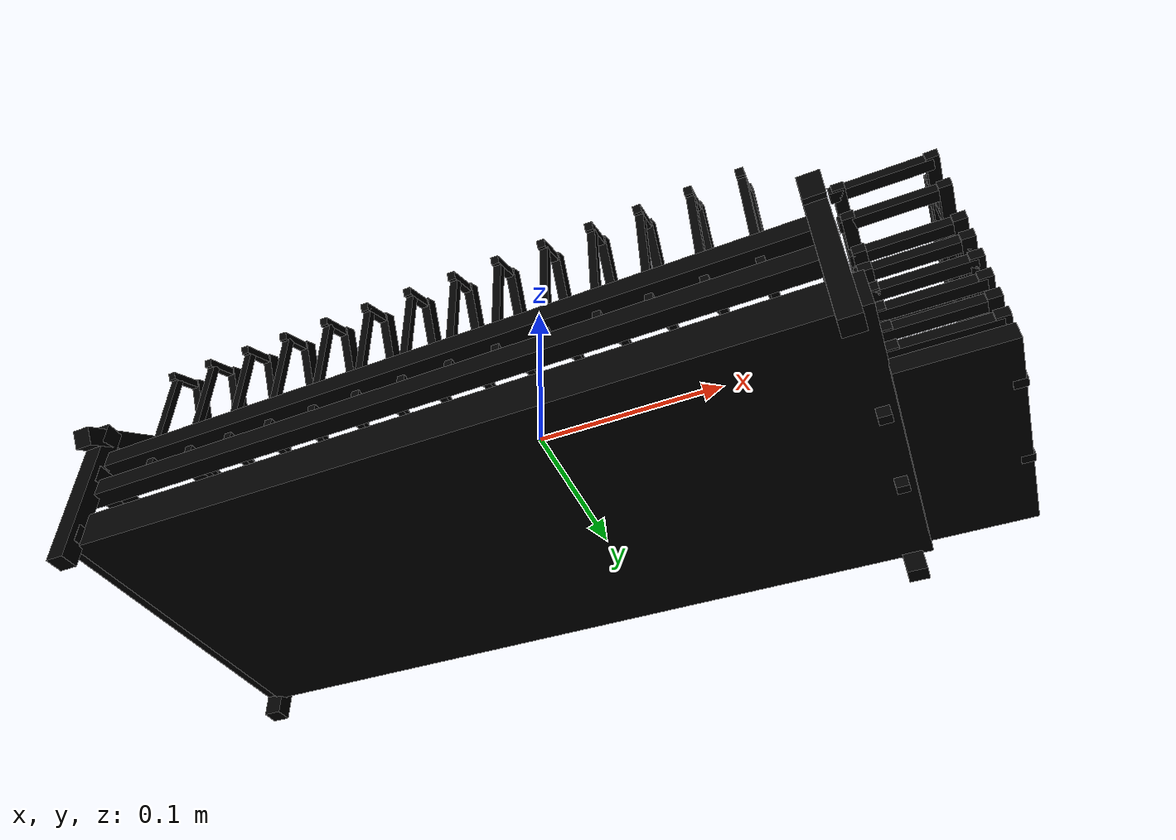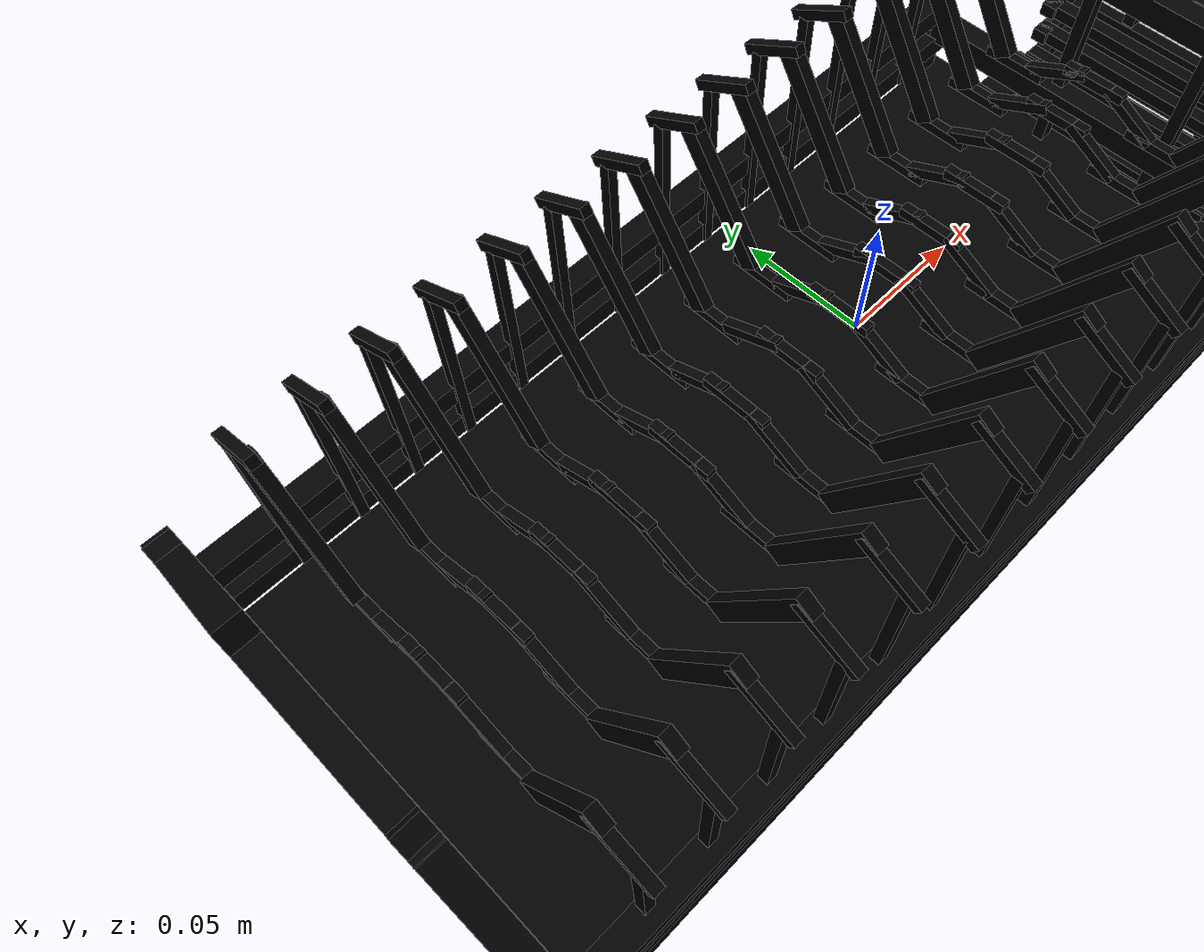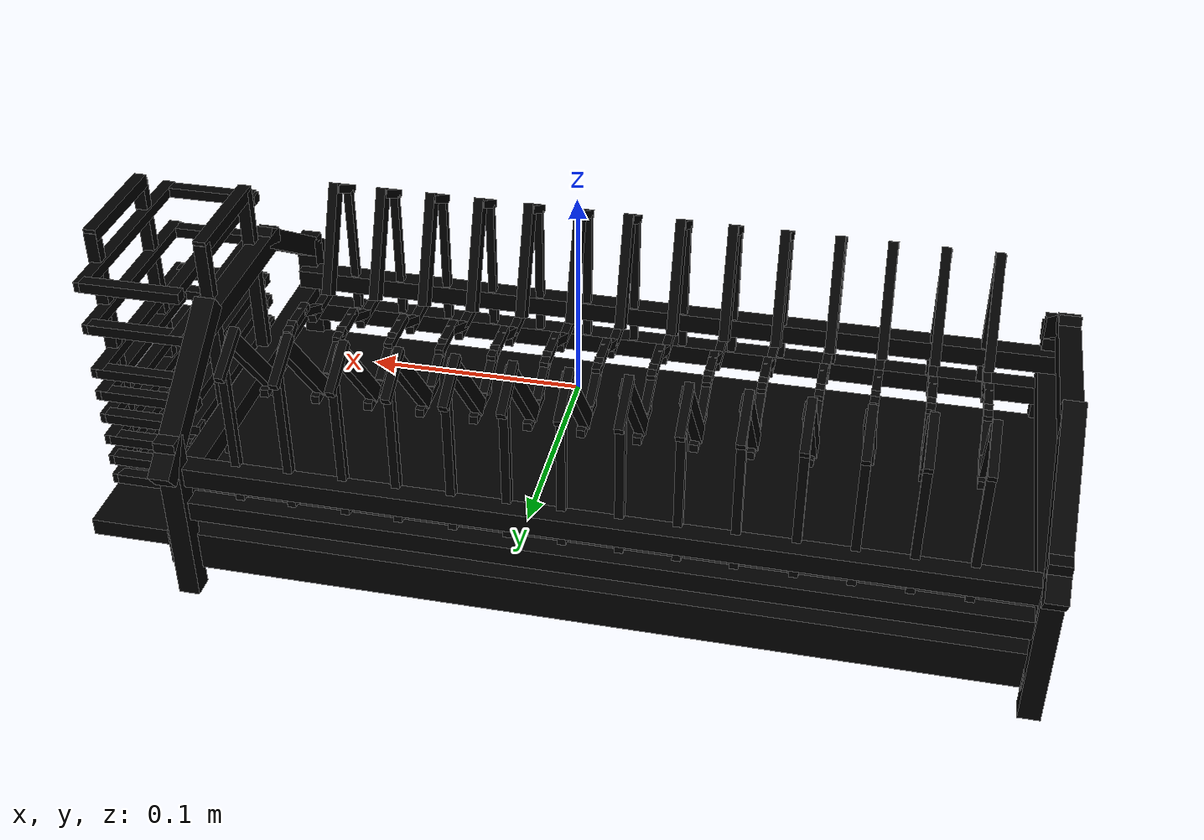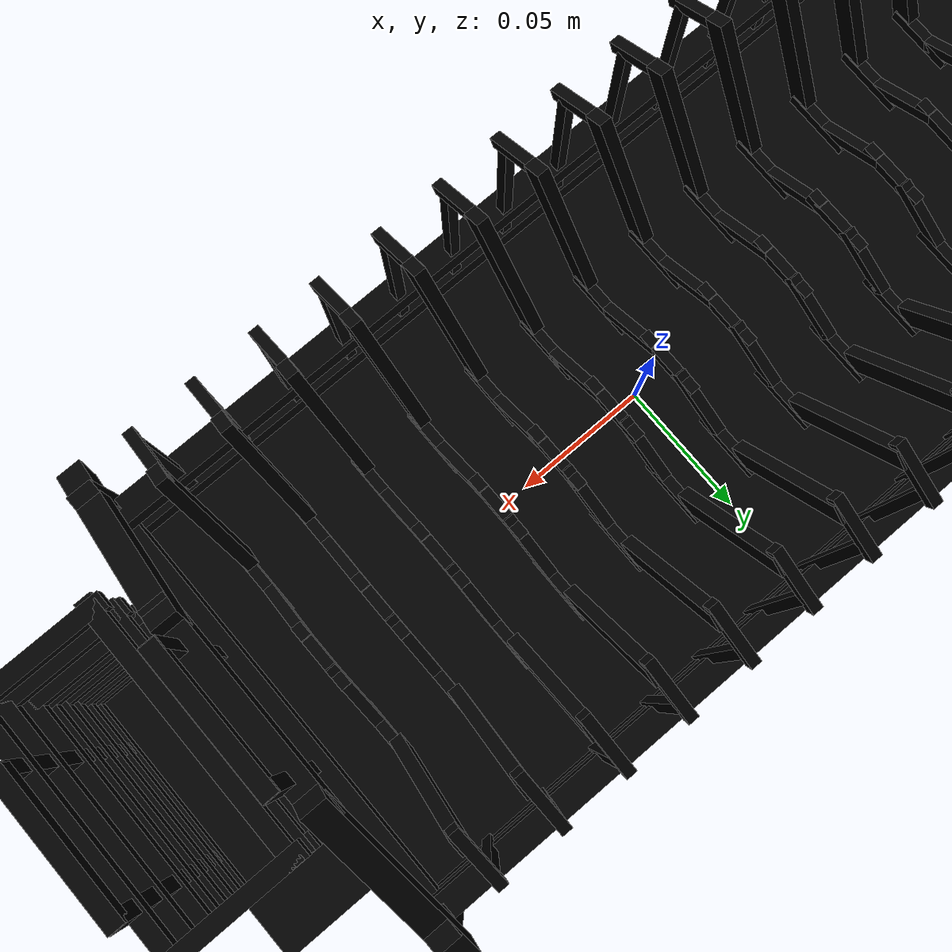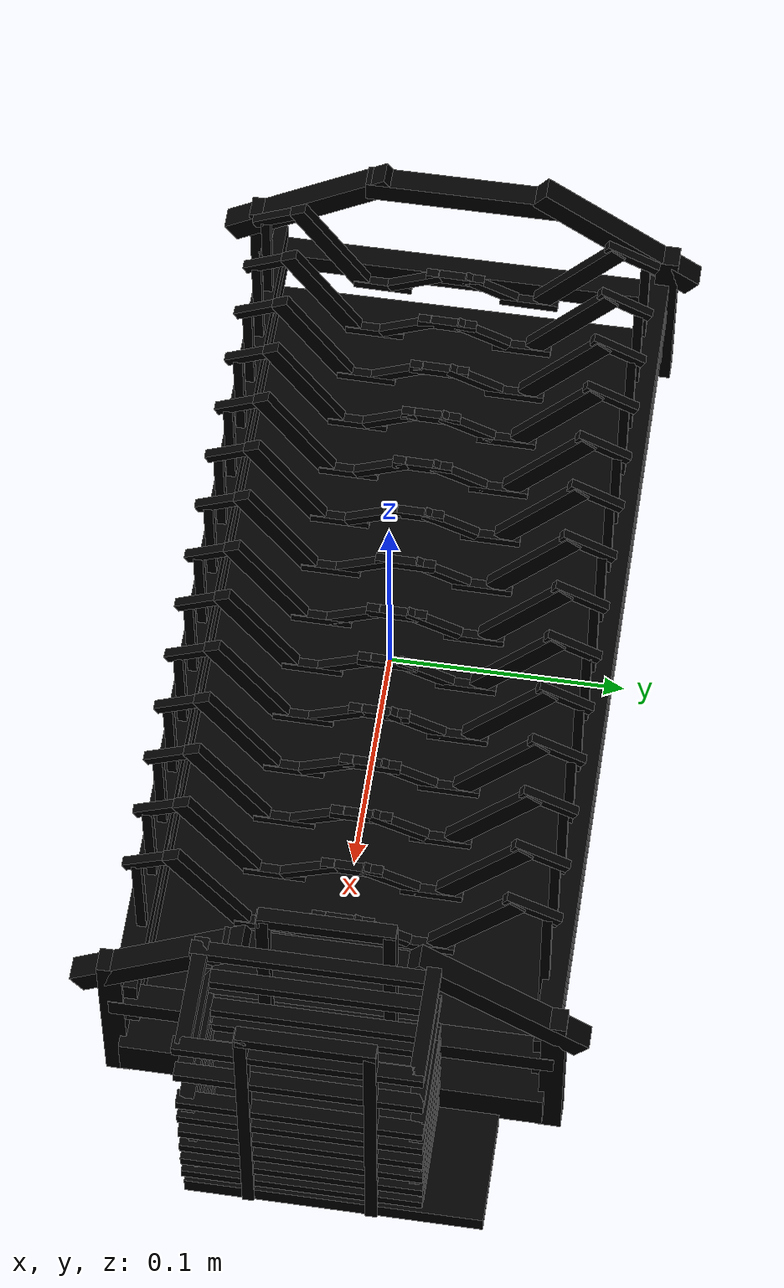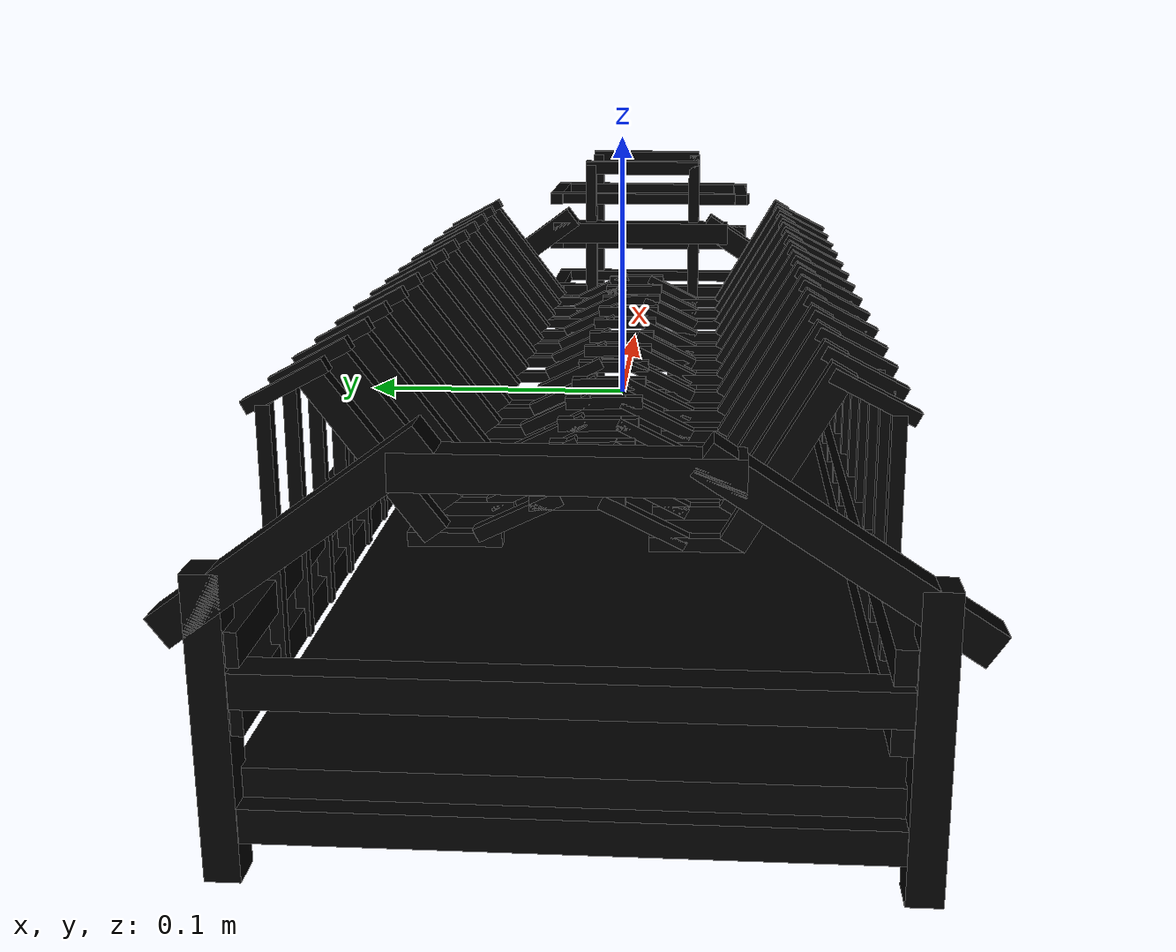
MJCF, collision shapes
<mujoco model="model">
  <option timestep="0.002" gravity="0.0 0.0 -9.81" />
  <compiler angle="radian" />
  <asset>
    <mesh file="visual/DishRack050.obj" name="DishRack050_vis" />
    <texture file="visual/T_BC001.png" name="DishRack050_material" type="2d" />
    <material name="DishRack050_material" rgba="1 1 1 1.0" texture="DishRack050_material" shininess="0.4472135901451111" specular="0.3103448502657381" />
  </asset>
  <default>
    <default class="visual">
      <geom conaffinity="0" contype="0" group="2" type="mesh" density="0" />
    </default>
    <default class="collision">
      <geom group="3" rgba="1 1 1 0.25" density="0" solref="0.004 1" solimp="0.998 0.998 0.001" friction="0.5" />
    </default>
    <default class="spawn">
      <geom group="0" rgba="1 1 1 0.5" contype="0" conaffinity="0" />
      <site group="0" rgba="1 1 1 0.5" />
    </default>
    <default class="region">
      <geom group="1" conaffinity="0" contype="0" rgba="0 1 0 0" mass="0" />
    </default>
  </default>
  <worldbody>
    <body>
      <body name="object">
        <geom mesh="DishRack050_vis" type="mesh" class="visual" material="DishRack050_material" group="2" contype="0" conaffinity="0" density="0" mass="0.5" />
        <geom type="box" pos="-0.02115616 0.00082735 -0.05501562" size="0.19703775644302368 0.08911336213350296 0.009812294505536556" quat="1.0 0.0 0.0 0.0" class="collision" group="3" rgba="0 0 0 0" density="0" friction="0.5" solref="0.004 1" solimp="0.998 0.998 0.001" />
        <geom type="box" pos="-0.21933006 0.00057172 -0.05883296" size="0.004999999888241291 0.09256390482187271 0.004999983124434948" quat="1.0 0.0 0.0 0.0" class="collision" group="3" rgba="0 0 0 0" density="0" friction="0.5" solref="0.004 1" solimp="0.998 0.998 0.001" />
        <geom type="box" pos="-0.21960633 0.09246731 -0.03200718" size="0.004999999888241291 0.00500000175088644 0.0434909425675869" quat="1.0 0.0 0.0 0.0" class="collision" group="3" rgba="0 0 0 0" density="0" friction="0.5" solref="0.004 1" solimp="0.998 0.998 0.001" />
        <geom type="box" pos="-0.21933006 0.00057172 -0.02034117" size="0.004999999888241291 0.09256390482187271 0.004999983590096235" quat="1.0 0.0 0.0 0.0" class="collision" group="3" rgba="0 0 0 0" density="0" friction="0.5" solref="0.004 1" solimp="0.998 0.998 0.001" />
        <geom type="box" pos="-0.21960633 -0.09057799 -0.03200718" size="0.004999999888241291 0.00500000175088644 0.043490950018167496" quat="1.0 0.0 0.0 0.0" class="collision" group="3" rgba="0 0 0 0" density="0" friction="0.5" solref="0.004 1" solimp="0.998 0.998 0.001" />
        <geom type="box" pos="-0.21960633 -0.06818052 0.01983970" size="0.004999999888241291 0.00500000175088644 0.043491180986166" quat="0.8804448246955872 -0.47414860129356384 0.0 0.0" class="collision" group="3" rgba="0 0 0 0" density="0" friction="0.5" solref="0.004 1" solimp="0.998 0.998 0.001" />
        <geom type="box" pos="-0.21960633 0.00060924 0.03899860" size="0.004999999888241291 0.0434911772608757 0.004999980330467224" quat="1.0 0.0 0.0 0.0" class="collision" group="3" rgba="0 0 0 0" density="0" friction="0.5" solref="0.004 1" solimp="0.998 0.998 0.001" />
        <geom type="box" pos="-0.21960633 0.06923353 0.02100375" size="0.004999999888241291 0.00500000175088644 0.043491180986166" quat="0.8926810622215271 0.4506889283657074 0.0 0.0" class="collision" group="3" rgba="0 0 0 0" density="0" friction="0.5" solref="0.004 1" solimp="0.998 0.998 0.001" />
        <geom type="box" pos="0.16583329 0.06923353 0.02100375" size="0.004999999888241291 0.00500000175088644 0.043491180986166" quat="0.8926810622215271 0.4506889283657074 0.0 0.0" class="collision" group="3" rgba="0 0 0 0" density="0" friction="0.5" solref="0.004 1" solimp="0.998 0.998 0.001" />
        <geom type="box" pos="0.16583329 0.00060924 0.03899860" size="0.004999999888241291 0.0434911772608757 0.004999980796128511" quat="1.0 0.0 0.0 0.0" class="collision" group="3" rgba="0 0 0 0" density="0" friction="0.5" solref="0.004 1" solimp="0.998 0.998 0.001" />
        <geom type="box" pos="0.16583329 -0.06818052 0.01983970" size="0.004999999888241291 0.00500000175088644 0.043491180986166" quat="0.8804448246955872 -0.47414860129356384 0.0 0.0" class="collision" group="3" rgba="0 0 0 0" density="0" friction="0.5" solref="0.004 1" solimp="0.998 0.998 0.001" />
        <geom type="box" pos="0.16583329 -0.09057799 -0.03200718" size="0.004999999888241291 0.00500000175088644 0.04349095746874809" quat="1.0 0.0 0.0 0.0" class="collision" group="3" rgba="0 0 0 0" density="0" friction="0.5" solref="0.004 1" solimp="0.998 0.998 0.001" />
        <geom type="box" pos="0.16610956 0.00057172 -0.02034117" size="0.004999999888241291 0.09256390482187271 0.0049999854527413845" quat="1.0 0.0 0.0 0.0" class="collision" group="3" rgba="0 0 0 0" density="0" friction="0.5" solref="0.004 1" solimp="0.998 0.998 0.001" />
        <geom type="box" pos="0.16583329 0.09246731 -0.03200718" size="0.004999999888241291 0.00500000175088644 0.04349096491932869" quat="1.0 0.0 0.0 0.0" class="collision" group="3" rgba="0 0 0 0" density="0" friction="0.5" solref="0.004 1" solimp="0.998 0.998 0.001" />
        <geom type="box" pos="0.19784509 -0.04953684 -0.05554686" size="0.02414286695420742 0.0030323867686092854 0.0025553666055202484" quat="1.0 0.0 0.0 0.0" class="collision" group="3" rgba="0 0 0 0" density="0" friction="0.5" solref="0.004 1" solimp="0.998 0.998 0.001" />
        <geom type="box" pos="-0.02734276 -0.08475694 -0.00918816" size="0.1962340921163559 0.0048832157626748085 0.004883221350610256" quat="1.0 0.0 0.0 0.0" class="collision" group="3" rgba="0 0 0 0" density="0" friction="0.5" solref="0.004 1" solimp="0.998 0.998 0.001" />
        <geom type="box" pos="-0.02734276 -0.08475694 -0.02835791" size="0.1962341070175171 0.004883216228336096 0.0048832218162715435" quat="1.0 0.0 0.0 0.0" class="collision" group="3" rgba="0 0 0 0" density="0" friction="0.5" solref="0.004 1" solimp="0.998 0.998 0.001" />
        <geom type="box" pos="-0.02734276 0.08900972 -0.02835791" size="0.19623412191867828 0.004883216693997383 0.004883222281932831" quat="1.0 0.0 0.0 0.0" class="collision" group="3" rgba="0 0 0 0" density="0" friction="0.5" solref="0.004 1" solimp="0.998 0.998 0.001" />
        <geom type="box" pos="-0.02734276 0.08900972 -0.00918816" size="0.19623413681983948 0.004883217625319958 0.004883222747594118" quat="1.0 0.0 0.0 0.0" class="collision" group="3" rgba="0 0 0 0" density="0" friction="0.5" solref="0.004 1" solimp="0.998 0.998 0.001" />
        <geom type="box" pos="0.19784509 0.04383259 -0.05554686" size="0.02414286695420742 0.0030323867686092854 0.0025553666055202484" quat="1.0 0.0 0.0 0.0" class="collision" group="3" rgba="0 0 0 0" density="0" friction="0.5" solref="0.004 1" solimp="0.998 0.998 0.001" />
        <geom type="box" pos="0.22162279 -0.00347440 -0.05554686" size="0.003032393753528595 0.05015871673822403 0.0025553666055202484" quat="1.0 0.0 0.0 0.0" class="collision" group="3" rgba="0 0 0 0" density="0" friction="0.5" solref="0.004 1" solimp="0.998 0.998 0.001" />
        <geom type="box" pos="0.17844625 -0.00347440 -0.05554686" size="0.003032393753528595 0.05015871673822403 0.0025553666055202484" quat="1.0 0.0 0.0 0.0" class="collision" group="3" rgba="0 0 0 0" density="0" friction="0.5" solref="0.004 1" solimp="0.998 0.998 0.001" />
        <geom type="box" pos="0.17844625 -0.00347440 -0.04411493" size="0.003032393753528595 0.05015871673822403 0.0025553666055202484" quat="1.0 0.0 0.0 0.0" class="collision" group="3" rgba="0 0 0 0" density="0" friction="0.5" solref="0.004 1" solimp="0.998 0.998 0.001" />
        <geom type="box" pos="0.22162279 -0.00347440 -0.04411493" size="0.003032393753528595 0.05015871673822403 0.0025553666055202484" quat="1.0 0.0 0.0 0.0" class="collision" group="3" rgba="0 0 0 0" density="0" friction="0.5" solref="0.004 1" solimp="0.998 0.998 0.001" />
        <geom type="box" pos="0.19784509 0.04383259 -0.04411493" size="0.02414286695420742 0.0030323867686092854 0.0025553666055202484" quat="1.0 0.0 0.0 0.0" class="collision" group="3" rgba="0 0 0 0" density="0" friction="0.5" solref="0.004 1" solimp="0.998 0.998 0.001" />
        <geom type="box" pos="0.19784509 -0.04953684 -0.04411493" size="0.02414286695420742 0.0030323867686092854 0.0025553666055202484" quat="1.0 0.0 0.0 0.0" class="collision" group="3" rgba="0 0 0 0" density="0" friction="0.5" solref="0.004 1" solimp="0.998 0.998 0.001" />
        <geom type="box" pos="0.17844625 -0.00347440 -0.03177803" size="0.003032393753528595 0.05015871673822403 0.0025553666055202484" quat="1.0 0.0 0.0 0.0" class="collision" group="3" rgba="0 0 0 0" density="0" friction="0.5" solref="0.004 1" solimp="0.998 0.998 0.001" />
        <geom type="box" pos="0.22162279 -0.00347440 -0.03177803" size="0.003032393753528595 0.05015871673822403 0.0025553666055202484" quat="1.0 0.0 0.0 0.0" class="collision" group="3" rgba="0 0 0 0" density="0" friction="0.5" solref="0.004 1" solimp="0.998 0.998 0.001" />
        <geom type="box" pos="0.19784509 0.04383259 -0.03177803" size="0.02414286695420742 0.0030323867686092854 0.0025553666055202484" quat="1.0 0.0 0.0 0.0" class="collision" group="3" rgba="0 0 0 0" density="0" friction="0.5" solref="0.004 1" solimp="0.998 0.998 0.001" />
        <geom type="box" pos="0.19784509 -0.04953684 -0.03177803" size="0.02414286695420742 0.0030323867686092854 0.0025553666055202484" quat="1.0 0.0 0.0 0.0" class="collision" group="3" rgba="0 0 0 0" density="0" friction="0.5" solref="0.004 1" solimp="0.998 0.998 0.001" />
        <geom type="box" pos="0.17844625 -0.00347440 -0.01899122" size="0.003032393753528595 0.05015871673822403 0.0025553666055202484" quat="1.0 0.0 0.0 0.0" class="collision" group="3" rgba="0 0 0 0" density="0" friction="0.5" solref="0.004 1" solimp="0.998 0.998 0.001" />
        <geom type="box" pos="0.22162279 -0.00347440 -0.01899122" size="0.003032393753528595 0.05015871673822403 0.0025553666055202484" quat="1.0 0.0 0.0 0.0" class="collision" group="3" rgba="0 0 0 0" density="0" friction="0.5" solref="0.004 1" solimp="0.998 0.998 0.001" />
        <geom type="box" pos="0.19784509 0.04383259 -0.01899122" size="0.02414286695420742 0.0030323867686092854 0.0025553666055202484" quat="1.0 0.0 0.0 0.0" class="collision" group="3" rgba="0 0 0 0" density="0" friction="0.5" solref="0.004 1" solimp="0.998 0.998 0.001" />
        <geom type="box" pos="0.19784509 -0.04953684 -0.01899122" size="0.02414286695420742 0.0030323867686092854 0.0025553666055202484" quat="1.0 0.0 0.0 0.0" class="collision" group="3" rgba="0 0 0 0" density="0" friction="0.5" solref="0.004 1" solimp="0.998 0.998 0.001" />
        <geom type="box" pos="0.17844625 -0.00347440 -0.00560479" size="0.003032393753528595 0.05015871673822403 0.0025553666055202484" quat="1.0 0.0 0.0 0.0" class="collision" group="3" rgba="0 0 0 0" density="0" friction="0.5" solref="0.004 1" solimp="0.998 0.998 0.001" />
        <geom type="box" pos="0.22162279 -0.00347440 -0.00560479" size="0.003032393753528595 0.05015871673822403 0.0025553666055202484" quat="1.0 0.0 0.0 0.0" class="collision" group="3" rgba="0 0 0 0" density="0" friction="0.5" solref="0.004 1" solimp="0.998 0.998 0.001" />
        <geom type="box" pos="0.19784509 0.04383259 -0.00560479" size="0.02414286695420742 0.0030323867686092854 0.0025553666055202484" quat="1.0 0.0 0.0 0.0" class="collision" group="3" rgba="0 0 0 0" density="0" friction="0.5" solref="0.004 1" solimp="0.998 0.998 0.001" />
        <geom type="box" pos="0.19784509 -0.04953684 -0.00560479" size="0.02414286695420742 0.0030323867686092854 0.0025553666055202484" quat="1.0 0.0 0.0 0.0" class="collision" group="3" rgba="0 0 0 0" density="0" friction="0.5" solref="0.004 1" solimp="0.998 0.998 0.001" />
        <geom type="box" pos="0.17844625 -0.00347440 0.00707240" size="0.003032393753528595 0.05015871673822403 0.0025553666055202484" quat="1.0 0.0 0.0 0.0" class="collision" group="3" rgba="0 0 0 0" density="0" friction="0.5" solref="0.004 1" solimp="0.998 0.998 0.001" />
        <geom type="box" pos="0.22162279 -0.00347440 0.00707240" size="0.003032393753528595 0.05015871673822403 0.0025553666055202484" quat="1.0 0.0 0.0 0.0" class="collision" group="3" rgba="0 0 0 0" density="0" friction="0.5" solref="0.004 1" solimp="0.998 0.998 0.001" />
        <geom type="box" pos="0.19784509 0.04383259 0.00707240" size="0.02414286695420742 0.0030323867686092854 0.0025553666055202484" quat="1.0 0.0 0.0 0.0" class="collision" group="3" rgba="0 0 0 0" density="0" friction="0.5" solref="0.004 1" solimp="0.998 0.998 0.001" />
        <geom type="box" pos="0.19784509 -0.04953684 0.00707240" size="0.02414286695420742 0.0030323867686092854 0.0025553666055202484" quat="1.0 0.0 0.0 0.0" class="collision" group="3" rgba="0 0 0 0" density="0" friction="0.5" solref="0.004 1" solimp="0.998 0.998 0.001" />
        <geom type="box" pos="0.17844625 -0.00347440 0.03158533" size="0.003032393753528595 0.05015871673822403 0.0025553666055202484" quat="1.0 0.0 0.0 0.0" class="collision" group="3" rgba="0 0 0 0" density="0" friction="0.5" solref="0.004 1" solimp="0.998 0.998 0.001" />
        <geom type="box" pos="0.22162279 -0.00347440 0.03158533" size="0.003032393753528595 0.05015871673822403 0.0025553666055202484" quat="1.0 0.0 0.0 0.0" class="collision" group="3" rgba="0 0 0 0" density="0" friction="0.5" solref="0.004 1" solimp="0.998 0.998 0.001" />
        <geom type="box" pos="0.19784509 0.04383259 0.03158533" size="0.02414286695420742 0.0030323867686092854 0.0025553666055202484" quat="1.0 0.0 0.0 0.0" class="collision" group="3" rgba="0 0 0 0" density="0" friction="0.5" solref="0.004 1" solimp="0.998 0.998 0.001" />
        <geom type="box" pos="0.19784509 -0.04953684 0.03158533" size="0.02414286695420742 0.0030323867686092854 0.0025553666055202484" quat="1.0 0.0 0.0 0.0" class="collision" group="3" rgba="0 0 0 0" density="0" friction="0.5" solref="0.004 1" solimp="0.998 0.998 0.001" />
        <geom type="box" pos="0.17844625 -0.00347440 0.05439672" size="0.003032393753528595 0.05015871673822403 0.0025553666055202484" quat="1.0 0.0 0.0 0.0" class="collision" group="3" rgba="0 0 0 0" density="0" friction="0.5" solref="0.004 1" solimp="0.998 0.998 0.001" />
        <geom type="box" pos="0.22162279 -0.00347440 0.05439672" size="0.003032393753528595 0.05015871673822403 0.0025553666055202484" quat="1.0 0.0 0.0 0.0" class="collision" group="3" rgba="0 0 0 0" density="0" friction="0.5" solref="0.004 1" solimp="0.998 0.998 0.001" />
        <geom type="box" pos="0.19784509 0.04383259 0.05439672" size="0.02414286695420742 0.0030323867686092854 0.0025553666055202484" quat="1.0 0.0 0.0 0.0" class="collision" group="3" rgba="0 0 0 0" density="0" friction="0.5" solref="0.004 1" solimp="0.998 0.998 0.001" />
        <geom type="box" pos="0.19784509 -0.04953684 0.05439672" size="0.02414286695420742 0.0030323867686092854 0.0025553666055202484" quat="1.0 0.0 0.0 0.0" class="collision" group="3" rgba="0 0 0 0" density="0" friction="0.5" solref="0.004 1" solimp="0.998 0.998 0.001" />
        <geom type="box" pos="0.16910948 -0.02584220 0.00081628" size="0.003032403066754341 0.0025553691666573286 0.07128959149122238" quat="1.0 0.0 0.0 0.0" class="collision" group="3" rgba="0 0 0 0" density="0" friction="0.5" solref="0.004 1" solimp="0.998 0.998 0.001" />
        <geom type="box" pos="0.16910948 0.02561059 0.00081628" size="0.003032403066754341 0.0025553691666573286 0.07128959149122238" quat="1.0 0.0 0.0 0.0" class="collision" group="3" rgba="0 0 0 0" density="0" friction="0.5" solref="0.004 1" solimp="0.998 0.998 0.001" />
        <geom type="box" pos="0.16910948 0.00009373 0.07085934" size="0.0030323935206979513 0.027848513796925545 0.003143641399219632" quat="1.0 0.0 0.0 0.0" class="collision" group="3" rgba="0 0 0 0" density="0" friction="0.5" solref="0.004 1" solimp="0.998 0.998 0.001" />
        <geom type="box" pos="0.22263829 0.00009373 0.07085934" size="0.0030323935206979513 0.027848513796925545 0.003143641632050276" quat="1.0 0.0 0.0 0.0" class="collision" group="3" rgba="0 0 0 0" density="0" friction="0.5" solref="0.004 1" solimp="0.998 0.998 0.001" />
        <geom type="box" pos="0.22263829 0.02561059 0.00081628" size="0.003032403066754341 0.0025553691666573286 0.07128959149122238" quat="1.0 0.0 0.0 0.0" class="collision" group="3" rgba="0 0 0 0" density="0" friction="0.5" solref="0.004 1" solimp="0.998 0.998 0.001" />
        <geom type="box" pos="0.22263829 -0.02584220 0.00081628" size="0.003032403066754341 0.0025553691666573286 0.07128959149122238" quat="1.0 0.0 0.0 0.0" class="collision" group="3" rgba="0 0 0 0" density="0" friction="0.5" solref="0.004 1" solimp="0.998 0.998 0.001" />
        <geom type="box" pos="-0.18751322 -0.08283846 0.00648969" size="0.0020000000949949026 0.0020000000949949026 0.038996532559394836" quat="1.0 0.0 0.0 0.0" class="collision" group="3" rgba="0 0 0 0" density="0" friction="0.5" solref="0.004 1" solimp="0.998 0.998 0.001" />
        <geom type="box" pos="-0.18751322 0.08475921 0.00648969" size="0.0020000000949949026 0.0020000000949949026 0.038996532559394836" quat="1.0 0.0 0.0 0.0" class="collision" group="3" rgba="0 0 0 0" density="0" friction="0.5" solref="0.004 1" solimp="0.998 0.998 0.001" />
        <geom type="box" pos="-0.18751322 0.07858811 0.05054504" size="0.0020000000949949026 0.0020000000949949026 0.012861630879342556" quat="0.8579508662223816 0.5137317776679993 0.0 0.0" class="collision" group="3" rgba="0 0 0 0" density="0" friction="0.5" solref="0.004 1" solimp="0.998 0.998 0.001" />
        <geom type="box" pos="-0.18764597 0.05598416 0.03252206" size="0.00231561460532248 0.0038496481720358133 0.027936508879065514" quat="0.31886813044548035 0.9475743174552917 -0.019563382491469383 -0.0065832724794745445" class="collision" group="3" rgba="0 0 0 0" density="0" friction="0.5" solref="0.004 1" solimp="0.998 0.998 0.001" />
        <geom type="box" pos="-0.18764597 -0.05438035 0.03316031" size="0.00231561460532248 0.0038496481720358133 0.027936505153775215" quat="0.259395033121109 -0.9655507206916809 0.012641362845897675 0.01631751097738743" class="collision" group="3" rgba="0 0 0 0" density="0" friction="0.5" solref="0.004 1" solimp="0.998 0.998 0.001" />
        <geom type="box" pos="-0.18751322 -0.07641044 0.05004504" size="0.0020000000949949026 0.0020000000949949026 0.01286163181066513" quat="0.5196169018745422 0.8543993234634399 0.0 0.0" class="collision" group="3" rgba="0 0 0 0" density="0" friction="0.5" solref="0.004 1" solimp="0.998 0.998 0.001" />
        <geom type="box" pos="-0.18751322 0.03432833 0.00868171" size="0.0020000000949949026 0.0020000000949949026 0.012861630879342556" quat="0.7135465145111084 0.7006078362464905 0.0 0.0" class="collision" group="3" rgba="0 0 0 0" density="0" friction="0.5" solref="0.004 1" solimp="0.998 0.998 0.001" />
        <geom type="box" pos="-0.18751322 -0.03101538 0.00868171" size="0.0020000000949949026 0.0020000000949949026 0.012861630879342556" quat="0.7135465145111084 0.7006078362464905 0.0 0.0" class="collision" group="3" rgba="0 0 0 0" density="0" friction="0.5" solref="0.004 1" solimp="0.998 0.998 0.001" />
        <geom type="box" pos="-0.18751322 -0.01664228 0.01448881" size="0.0020000000949949026 0.0020000000949949026 0.01286163181066513" quat="0.5267975330352783 0.8499907851219177 0.0 0.0" class="collision" group="3" rgba="0 0 0 0" density="0" friction="0.5" solref="0.004 1" solimp="0.998 0.998 0.001" />
        <geom type="box" pos="-0.18751322 0.01696871 0.01543445" size="0.0020000000949949026 0.0020000000949949026 0.012861632741987705" quat="0.847457766532898 0.5308628678321838 0.0 0.0" class="collision" group="3" rgba="0 0 0 0" density="0" friction="0.5" solref="0.004 1" solimp="0.998 0.998 0.001" />
        <geom type="box" pos="-0.18751322 0.00114079 0.01971562" size="0.0020000000949949026 0.0020000003278255463 0.01286163181066513" quat="0.7150533199310303 0.6990699172019958 0.0 0.0" class="collision" group="3" rgba="0 0 0 0" density="0" friction="0.5" solref="0.004 1" solimp="0.998 0.998 0.001" />
        <geom type="box" pos="-0.16259052 0.00114079 0.01971562" size="0.0020000000949949026 0.0020000003278255463 0.01286163181066513" quat="0.7150533199310303 0.6990699172019958 0.0 0.0" class="collision" group="3" rgba="0 0 0 0" density="0" friction="0.5" solref="0.004 1" solimp="0.998 0.998 0.001" />
        <geom type="box" pos="-0.16259052 0.01696871 0.01543445" size="0.0020000000949949026 0.0020000000949949026 0.012861632741987705" quat="0.847457766532898 0.5308628678321838 0.0 0.0" class="collision" group="3" rgba="0 0 0 0" density="0" friction="0.5" solref="0.004 1" solimp="0.998 0.998 0.001" />
        <geom type="box" pos="-0.16259052 -0.01664228 0.01448881" size="0.0020000000949949026 0.0020000000949949026 0.01286163181066513" quat="0.5267975330352783 0.8499907851219177 0.0 0.0" class="collision" group="3" rgba="0 0 0 0" density="0" friction="0.5" solref="0.004 1" solimp="0.998 0.998 0.001" />
        <geom type="box" pos="-0.16259052 -0.03101538 0.00868171" size="0.0020000000949949026 0.0020000000949949026 0.012861630879342556" quat="0.7135465145111084 0.7006078362464905 0.0 0.0" class="collision" group="3" rgba="0 0 0 0" density="0" friction="0.5" solref="0.004 1" solimp="0.998 0.998 0.001" />
        <geom type="box" pos="-0.16259052 0.03432833 0.00868171" size="0.0020000000949949026 0.0020000000949949026 0.012861630879342556" quat="0.7135465145111084 0.7006078362464905 0.0 0.0" class="collision" group="3" rgba="0 0 0 0" density="0" friction="0.5" solref="0.004 1" solimp="0.998 0.998 0.001" />
        <geom type="box" pos="-0.16259052 -0.07641044 0.05004504" size="0.0020000000949949026 0.0020000000949949026 0.01286163181066513" quat="0.5196169018745422 0.8543993234634399 0.0 0.0" class="collision" group="3" rgba="0 0 0 0" density="0" friction="0.5" solref="0.004 1" solimp="0.998 0.998 0.001" />
        <geom type="box" pos="-0.16272327 -0.05438035 0.03316031" size="0.00231561460532248 0.0038496481720358133 0.027936505153775215" quat="0.259395033121109 -0.9655507206916809 0.012641362845897675 0.01631751097738743" class="collision" group="3" rgba="0 0 0 0" density="0" friction="0.5" solref="0.004 1" solimp="0.998 0.998 0.001" />
        <geom type="box" pos="-0.16272327 0.05598416 0.03252206" size="0.00231561460532248 0.0038496481720358133 0.027936508879065514" quat="0.31886813044548035 0.9475743174552917 -0.019563382491469383 -0.0065832724794745445" class="collision" group="3" rgba="0 0 0 0" density="0" friction="0.5" solref="0.004 1" solimp="0.998 0.998 0.001" />
        <geom type="box" pos="-0.16259052 0.07858811 0.05054504" size="0.0020000000949949026 0.0020000000949949026 0.012861630879342556" quat="0.8579508662223816 0.5137317776679993 0.0 0.0" class="collision" group="3" rgba="0 0 0 0" density="0" friction="0.5" solref="0.004 1" solimp="0.998 0.998 0.001" />
        <geom type="box" pos="-0.16259052 0.08475921 0.00648969" size="0.0020000000949949026 0.0020000000949949026 0.038996532559394836" quat="1.0 0.0 0.0 0.0" class="collision" group="3" rgba="0 0 0 0" density="0" friction="0.5" solref="0.004 1" solimp="0.998 0.998 0.001" />
        <geom type="box" pos="-0.16259052 -0.08283846 0.00648969" size="0.0020000000949949026 0.0020000000949949026 0.038996532559394836" quat="1.0 0.0 0.0 0.0" class="collision" group="3" rgba="0 0 0 0" density="0" friction="0.5" solref="0.004 1" solimp="0.998 0.998 0.001" />
        <geom type="box" pos="-0.13785014 -0.08283846 0.00648969" size="0.0020000000949949026 0.0020000000949949026 0.038996532559394836" quat="1.0 0.0 0.0 0.0" class="collision" group="3" rgba="0 0 0 0" density="0" friction="0.5" solref="0.004 1" solimp="0.998 0.998 0.001" />
        <geom type="box" pos="-0.13785014 0.08475921 0.00648969" size="0.0020000000949949026 0.0020000000949949026 0.038996532559394836" quat="1.0 0.0 0.0 0.0" class="collision" group="3" rgba="0 0 0 0" density="0" friction="0.5" solref="0.004 1" solimp="0.998 0.998 0.001" />
        <geom type="box" pos="-0.13785014 0.07858811 0.05054504" size="0.0020000000949949026 0.0020000000949949026 0.012861630879342556" quat="0.8579508662223816 0.5137317776679993 0.0 0.0" class="collision" group="3" rgba="0 0 0 0" density="0" friction="0.5" solref="0.004 1" solimp="0.998 0.998 0.001" />
        <geom type="box" pos="-0.13798289 0.05598416 0.03252206" size="0.00231561460532248 0.0038496481720358133 0.027936508879065514" quat="0.31886813044548035 0.9475743174552917 -0.019563382491469383 -0.0065832724794745445" class="collision" group="3" rgba="0 0 0 0" density="0" friction="0.5" solref="0.004 1" solimp="0.998 0.998 0.001" />
        <geom type="box" pos="-0.13798289 -0.05438035 0.03316031" size="0.00231561460532248 0.0038496481720358133 0.027936505153775215" quat="0.259395033121109 -0.9655507206916809 0.012641362845897675 0.01631751097738743" class="collision" group="3" rgba="0 0 0 0" density="0" friction="0.5" solref="0.004 1" solimp="0.998 0.998 0.001" />
        <geom type="box" pos="-0.13785014 -0.07641044 0.05004504" size="0.0020000000949949026 0.0020000000949949026 0.01286163181066513" quat="0.5196169018745422 0.8543993234634399 0.0 0.0" class="collision" group="3" rgba="0 0 0 0" density="0" friction="0.5" solref="0.004 1" solimp="0.998 0.998 0.001" />
        <geom type="box" pos="-0.13785014 0.03432833 0.00868171" size="0.0020000000949949026 0.0020000000949949026 0.012861630879342556" quat="0.7135465145111084 0.7006078362464905 0.0 0.0" class="collision" group="3" rgba="0 0 0 0" density="0" friction="0.5" solref="0.004 1" solimp="0.998 0.998 0.001" />
        <geom type="box" pos="-0.13785014 -0.03101538 0.00868171" size="0.0020000000949949026 0.0020000000949949026 0.012861630879342556" quat="0.7135465145111084 0.7006078362464905 0.0 0.0" class="collision" group="3" rgba="0 0 0 0" density="0" friction="0.5" solref="0.004 1" solimp="0.998 0.998 0.001" />
        <geom type="box" pos="-0.13785014 -0.01664228 0.01448881" size="0.0020000000949949026 0.0020000000949949026 0.01286163181066513" quat="0.5267975330352783 0.8499907851219177 0.0 0.0" class="collision" group="3" rgba="0 0 0 0" density="0" friction="0.5" solref="0.004 1" solimp="0.998 0.998 0.001" />
        <geom type="box" pos="-0.13785014 0.01696871 0.01543445" size="0.0020000000949949026 0.0020000000949949026 0.012861632741987705" quat="0.847457766532898 0.5308628678321838 0.0 0.0" class="collision" group="3" rgba="0 0 0 0" density="0" friction="0.5" solref="0.004 1" solimp="0.998 0.998 0.001" />
        <geom type="box" pos="-0.13785014 0.00114079 0.01971562" size="0.0020000000949949026 0.0020000003278255463 0.01286163181066513" quat="0.7150533199310303 0.6990699172019958 0.0 0.0" class="collision" group="3" rgba="0 0 0 0" density="0" friction="0.5" solref="0.004 1" solimp="0.998 0.998 0.001" />
        <geom type="box" pos="-0.11310972 0.00114079 0.01971562" size="0.0020000000949949026 0.0020000003278255463 0.01286163181066513" quat="0.7150533199310303 0.6990699172019958 0.0 0.0" class="collision" group="3" rgba="0 0 0 0" density="0" friction="0.5" solref="0.004 1" solimp="0.998 0.998 0.001" />
        <geom type="box" pos="-0.11310972 0.01696871 0.01543445" size="0.0020000000949949026 0.0020000000949949026 0.012861632741987705" quat="0.847457766532898 0.5308628678321838 0.0 0.0" class="collision" group="3" rgba="0 0 0 0" density="0" friction="0.5" solref="0.004 1" solimp="0.998 0.998 0.001" />
        <geom type="box" pos="-0.11310972 -0.01664228 0.01448881" size="0.0020000000949949026 0.0020000000949949026 0.01286163181066513" quat="0.5267975330352783 0.8499907851219177 0.0 0.0" class="collision" group="3" rgba="0 0 0 0" density="0" friction="0.5" solref="0.004 1" solimp="0.998 0.998 0.001" />
        <geom type="box" pos="-0.11310972 -0.03101538 0.00868171" size="0.0020000000949949026 0.0020000000949949026 0.012861630879342556" quat="0.7135465145111084 0.7006078362464905 0.0 0.0" class="collision" group="3" rgba="0 0 0 0" density="0" friction="0.5" solref="0.004 1" solimp="0.998 0.998 0.001" />
        <geom type="box" pos="-0.11310972 0.03432833 0.00868171" size="0.0020000000949949026 0.0020000000949949026 0.012861630879342556" quat="0.7135465145111084 0.7006078362464905 0.0 0.0" class="collision" group="3" rgba="0 0 0 0" density="0" friction="0.5" solref="0.004 1" solimp="0.998 0.998 0.001" />
        <geom type="box" pos="-0.11310972 -0.07641044 0.05004504" size="0.0020000000949949026 0.0020000000949949026 0.01286163181066513" quat="0.5196169018745422 0.8543993234634399 0.0 0.0" class="collision" group="3" rgba="0 0 0 0" density="0" friction="0.5" solref="0.004 1" solimp="0.998 0.998 0.001" />
        <geom type="box" pos="-0.11324246 -0.05438035 0.03316031" size="0.00231561460532248 0.0038496481720358133 0.027936505153775215" quat="0.259395033121109 -0.9655507206916809 0.012641362845897675 0.01631751097738743" class="collision" group="3" rgba="0 0 0 0" density="0" friction="0.5" solref="0.004 1" solimp="0.998 0.998 0.001" />
        <geom type="box" pos="-0.11324246 0.05598416 0.03252206" size="0.00231561460532248 0.0038496481720358133 0.027936508879065514" quat="0.31886813044548035 0.9475743174552917 -0.019563382491469383 -0.0065832724794745445" class="collision" group="3" rgba="0 0 0 0" density="0" friction="0.5" solref="0.004 1" solimp="0.998 0.998 0.001" />
        <geom type="box" pos="-0.11310972 0.07858811 0.05054504" size="0.0020000000949949026 0.0020000000949949026 0.012861630879342556" quat="0.8579508662223816 0.5137317776679993 0.0 0.0" class="collision" group="3" rgba="0 0 0 0" density="0" friction="0.5" solref="0.004 1" solimp="0.998 0.998 0.001" />
        <geom type="box" pos="-0.11310972 0.08475921 0.00648969" size="0.0020000000949949026 0.0020000000949949026 0.038996532559394836" quat="1.0 0.0 0.0 0.0" class="collision" group="3" rgba="0 0 0 0" density="0" friction="0.5" solref="0.004 1" solimp="0.998 0.998 0.001" />
        <geom type="box" pos="-0.11310972 -0.08283846 0.00648969" size="0.0020000000949949026 0.0020000000949949026 0.038996532559394836" quat="1.0 0.0 0.0 0.0" class="collision" group="3" rgba="0 0 0 0" density="0" friction="0.5" solref="0.004 1" solimp="0.998 0.998 0.001" />
        <geom type="box" pos="-0.08721852 -0.08283846 0.00648969" size="0.0020000000949949026 0.0020000000949949026 0.038996532559394836" quat="1.0 0.0 0.0 0.0" class="collision" group="3" rgba="0 0 0 0" density="0" friction="0.5" solref="0.004 1" solimp="0.998 0.998 0.001" />
        <geom type="box" pos="-0.08721852 0.08475921 0.00648969" size="0.0020000000949949026 0.0020000000949949026 0.038996532559394836" quat="1.0 0.0 0.0 0.0" class="collision" group="3" rgba="0 0 0 0" density="0" friction="0.5" solref="0.004 1" solimp="0.998 0.998 0.001" />
        <geom type="box" pos="-0.08721852 0.07858811 0.05054504" size="0.0020000000949949026 0.0020000000949949026 0.012861630879342556" quat="0.8579508662223816 0.5137317776679993 0.0 0.0" class="collision" group="3" rgba="0 0 0 0" density="0" friction="0.5" solref="0.004 1" solimp="0.998 0.998 0.001" />
        <geom type="box" pos="-0.08735127 0.05598416 0.03252206" size="0.00231561460532248 0.0038496481720358133 0.027936508879065514" quat="0.31886813044548035 0.9475743174552917 -0.019563382491469383 -0.0065832724794745445" class="collision" group="3" rgba="0 0 0 0" density="0" friction="0.5" solref="0.004 1" solimp="0.998 0.998 0.001" />
        <geom type="box" pos="-0.08735127 -0.05438035 0.03316031" size="0.00231561460532248 0.0038496481720358133 0.027936505153775215" quat="0.259395033121109 -0.9655507206916809 0.012641362845897675 0.01631751097738743" class="collision" group="3" rgba="0 0 0 0" density="0" friction="0.5" solref="0.004 1" solimp="0.998 0.998 0.001" />
        <geom type="box" pos="-0.08721852 -0.07641044 0.05004504" size="0.0020000000949949026 0.0020000000949949026 0.01286163181066513" quat="0.5196169018745422 0.8543993234634399 0.0 0.0" class="collision" group="3" rgba="0 0 0 0" density="0" friction="0.5" solref="0.004 1" solimp="0.998 0.998 0.001" />
        <geom type="box" pos="-0.08721852 0.03432833 0.00868171" size="0.0020000000949949026 0.0020000000949949026 0.012861630879342556" quat="0.7135465145111084 0.7006078362464905 0.0 0.0" class="collision" group="3" rgba="0 0 0 0" density="0" friction="0.5" solref="0.004 1" solimp="0.998 0.998 0.001" />
        <geom type="box" pos="-0.08721852 -0.03101538 0.00868171" size="0.0020000000949949026 0.0020000000949949026 0.012861630879342556" quat="0.7135465145111084 0.7006078362464905 0.0 0.0" class="collision" group="3" rgba="0 0 0 0" density="0" friction="0.5" solref="0.004 1" solimp="0.998 0.998 0.001" />
        <geom type="box" pos="-0.08721852 -0.01664228 0.01448881" size="0.0020000000949949026 0.0020000000949949026 0.01286163181066513" quat="0.5267975330352783 0.8499907851219177 0.0 0.0" class="collision" group="3" rgba="0 0 0 0" density="0" friction="0.5" solref="0.004 1" solimp="0.998 0.998 0.001" />
        <geom type="box" pos="-0.08721852 0.01696871 0.01543445" size="0.0020000000949949026 0.0020000000949949026 0.012861632741987705" quat="0.847457766532898 0.5308628678321838 0.0 0.0" class="collision" group="3" rgba="0 0 0 0" density="0" friction="0.5" solref="0.004 1" solimp="0.998 0.998 0.001" />
        <geom type="box" pos="-0.08721852 0.00114079 0.01971562" size="0.0020000000949949026 0.0020000003278255463 0.01286163181066513" quat="0.7150533199310303 0.6990699172019958 0.0 0.0" class="collision" group="3" rgba="0 0 0 0" density="0" friction="0.5" solref="0.004 1" solimp="0.998 0.998 0.001" />
        <geom type="box" pos="-0.06222702 0.00114079 0.01971562" size="0.0020000000949949026 0.0020000003278255463 0.01286163181066513" quat="0.7150533199310303 0.6990699172019958 0.0 0.0" class="collision" group="3" rgba="0 0 0 0" density="0" friction="0.5" solref="0.004 1" solimp="0.998 0.998 0.001" />
        <geom type="box" pos="-0.06222702 0.01696871 0.01543445" size="0.0020000000949949026 0.0020000000949949026 0.012861632741987705" quat="0.847457766532898 0.5308628678321838 0.0 0.0" class="collision" group="3" rgba="0 0 0 0" density="0" friction="0.5" solref="0.004 1" solimp="0.998 0.998 0.001" />
        <geom type="box" pos="-0.06222702 -0.01664228 0.01448881" size="0.0020000000949949026 0.0020000000949949026 0.01286163181066513" quat="0.5267975330352783 0.8499907851219177 0.0 0.0" class="collision" group="3" rgba="0 0 0 0" density="0" friction="0.5" solref="0.004 1" solimp="0.998 0.998 0.001" />
        <geom type="box" pos="-0.06222702 -0.03101538 0.00868171" size="0.0020000000949949026 0.0020000000949949026 0.012861630879342556" quat="0.7135465145111084 0.7006078362464905 0.0 0.0" class="collision" group="3" rgba="0 0 0 0" density="0" friction="0.5" solref="0.004 1" solimp="0.998 0.998 0.001" />
        <geom type="box" pos="-0.06222702 0.03432833 0.00868171" size="0.0020000000949949026 0.0020000000949949026 0.012861630879342556" quat="0.7135465145111084 0.7006078362464905 0.0 0.0" class="collision" group="3" rgba="0 0 0 0" density="0" friction="0.5" solref="0.004 1" solimp="0.998 0.998 0.001" />
        <geom type="box" pos="-0.06222702 -0.07641044 0.05004504" size="0.0020000000949949026 0.0020000000949949026 0.01286163181066513" quat="0.5196169018745422 0.8543993234634399 0.0 0.0" class="collision" group="3" rgba="0 0 0 0" density="0" friction="0.5" solref="0.004 1" solimp="0.998 0.998 0.001" />
        <geom type="box" pos="-0.06235977 -0.05438035 0.03316031" size="0.00231561460532248 0.0038496481720358133 0.027936505153775215" quat="0.259395033121109 -0.9655507206916809 0.012641362845897675 0.01631751097738743" class="collision" group="3" rgba="0 0 0 0" density="0" friction="0.5" solref="0.004 1" solimp="0.998 0.998 0.001" />
        <geom type="box" pos="-0.06235977 0.05598416 0.03252206" size="0.00231561460532248 0.0038496481720358133 0.027936508879065514" quat="0.31886813044548035 0.9475743174552917 -0.019563382491469383 -0.0065832724794745445" class="collision" group="3" rgba="0 0 0 0" density="0" friction="0.5" solref="0.004 1" solimp="0.998 0.998 0.001" />
        <geom type="box" pos="-0.06222702 0.07858811 0.05054504" size="0.0020000000949949026 0.0020000000949949026 0.012861630879342556" quat="0.8579508662223816 0.5137317776679993 0.0 0.0" class="collision" group="3" rgba="0 0 0 0" density="0" friction="0.5" solref="0.004 1" solimp="0.998 0.998 0.001" />
        <geom type="box" pos="-0.06222702 0.08475921 0.00648969" size="0.0020000000949949026 0.0020000000949949026 0.038996532559394836" quat="1.0 0.0 0.0 0.0" class="collision" group="3" rgba="0 0 0 0" density="0" friction="0.5" solref="0.004 1" solimp="0.998 0.998 0.001" />
        <geom type="box" pos="-0.06222702 -0.08283846 0.00648969" size="0.0020000000949949026 0.0020000000949949026 0.038996532559394836" quat="1.0 0.0 0.0 0.0" class="collision" group="3" rgba="0 0 0 0" density="0" friction="0.5" solref="0.004 1" solimp="0.998 0.998 0.001" />
        <geom type="box" pos="-0.03673694 -0.08283846 0.00648969" size="0.0020000000949949026 0.0020000000949949026 0.038996532559394836" quat="1.0 0.0 0.0 0.0" class="collision" group="3" rgba="0 0 0 0" density="0" friction="0.5" solref="0.004 1" solimp="0.998 0.998 0.001" />
        <geom type="box" pos="-0.03673694 0.08475921 0.00648969" size="0.0020000000949949026 0.0020000000949949026 0.038996532559394836" quat="1.0 0.0 0.0 0.0" class="collision" group="3" rgba="0 0 0 0" density="0" friction="0.5" solref="0.004 1" solimp="0.998 0.998 0.001" />
        <geom type="box" pos="-0.03673694 0.07858811 0.05054504" size="0.0020000000949949026 0.0020000000949949026 0.012861630879342556" quat="0.8579508662223816 0.5137317776679993 0.0 0.0" class="collision" group="3" rgba="0 0 0 0" density="0" friction="0.5" solref="0.004 1" solimp="0.998 0.998 0.001" />
        <geom type="box" pos="-0.03686969 0.05598416 0.03252206" size="0.00231561460532248 0.0038496481720358133 0.027936508879065514" quat="0.31886813044548035 0.9475743174552917 -0.019563382491469383 -0.0065832724794745445" class="collision" group="3" rgba="0 0 0 0" density="0" friction="0.5" solref="0.004 1" solimp="0.998 0.998 0.001" />
        <geom type="box" pos="-0.03686969 -0.05438035 0.03316031" size="0.00231561460532248 0.0038496481720358133 0.027936505153775215" quat="0.259395033121109 -0.9655507206916809 0.012641362845897675 0.01631751097738743" class="collision" group="3" rgba="0 0 0 0" density="0" friction="0.5" solref="0.004 1" solimp="0.998 0.998 0.001" />
        <geom type="box" pos="-0.03673694 -0.07641044 0.05004504" size="0.0020000000949949026 0.0020000000949949026 0.01286163181066513" quat="0.5196169018745422 0.8543993234634399 0.0 0.0" class="collision" group="3" rgba="0 0 0 0" density="0" friction="0.5" solref="0.004 1" solimp="0.998 0.998 0.001" />
        <geom type="box" pos="-0.03673694 0.03432833 0.00868171" size="0.0020000000949949026 0.0020000000949949026 0.012861630879342556" quat="0.7135465145111084 0.7006078362464905 0.0 0.0" class="collision" group="3" rgba="0 0 0 0" density="0" friction="0.5" solref="0.004 1" solimp="0.998 0.998 0.001" />
        <geom type="box" pos="-0.03673694 -0.03101538 0.00868171" size="0.0020000000949949026 0.0020000000949949026 0.012861630879342556" quat="0.7135465145111084 0.7006078362464905 0.0 0.0" class="collision" group="3" rgba="0 0 0 0" density="0" friction="0.5" solref="0.004 1" solimp="0.998 0.998 0.001" />
        <geom type="box" pos="-0.03673694 -0.01664228 0.01448881" size="0.0020000000949949026 0.0020000000949949026 0.01286163181066513" quat="0.5267975330352783 0.8499907851219177 0.0 0.0" class="collision" group="3" rgba="0 0 0 0" density="0" friction="0.5" solref="0.004 1" solimp="0.998 0.998 0.001" />
        <geom type="box" pos="-0.03673694 0.01696871 0.01543445" size="0.0020000000949949026 0.0020000000949949026 0.012861632741987705" quat="0.847457766532898 0.5308628678321838 0.0 0.0" class="collision" group="3" rgba="0 0 0 0" density="0" friction="0.5" solref="0.004 1" solimp="0.998 0.998 0.001" />
        <geom type="box" pos="-0.03673694 0.00114079 0.01971562" size="0.0020000000949949026 0.0020000003278255463 0.01286163181066513" quat="0.7150533199310303 0.6990699172019958 0.0 0.0" class="collision" group="3" rgba="0 0 0 0" density="0" friction="0.5" solref="0.004 1" solimp="0.998 0.998 0.001" />
        <geom type="box" pos="-0.01123111 0.00114079 0.01971562" size="0.0020000000949949026 0.0020000003278255463 0.01286163181066513" quat="0.7150533199310303 0.6990699172019958 0.0 0.0" class="collision" group="3" rgba="0 0 0 0" density="0" friction="0.5" solref="0.004 1" solimp="0.998 0.998 0.001" />
        <geom type="box" pos="-0.01123111 0.01696871 0.01543445" size="0.0020000000949949026 0.0020000000949949026 0.012861632741987705" quat="0.847457766532898 0.5308628678321838 0.0 0.0" class="collision" group="3" rgba="0 0 0 0" density="0" friction="0.5" solref="0.004 1" solimp="0.998 0.998 0.001" />
        <geom type="box" pos="-0.01123111 -0.01664228 0.01448881" size="0.0020000000949949026 0.0020000000949949026 0.01286163181066513" quat="0.5267975330352783 0.8499907851219177 0.0 0.0" class="collision" group="3" rgba="0 0 0 0" density="0" friction="0.5" solref="0.004 1" solimp="0.998 0.998 0.001" />
        <geom type="box" pos="-0.01123111 -0.03101538 0.00868171" size="0.0020000000949949026 0.0020000000949949026 0.012861630879342556" quat="0.7135465145111084 0.7006078362464905 0.0 0.0" class="collision" group="3" rgba="0 0 0 0" density="0" friction="0.5" solref="0.004 1" solimp="0.998 0.998 0.001" />
        <geom type="box" pos="-0.01123111 0.03432833 0.00868171" size="0.0020000000949949026 0.0020000000949949026 0.012861630879342556" quat="0.7135465145111084 0.7006078362464905 0.0 0.0" class="collision" group="3" rgba="0 0 0 0" density="0" friction="0.5" solref="0.004 1" solimp="0.998 0.998 0.001" />
        <geom type="box" pos="-0.01123111 -0.07641044 0.05004504" size="0.0020000000949949026 0.0020000000949949026 0.01286163181066513" quat="0.5196169018745422 0.8543993234634399 0.0 0.0" class="collision" group="3" rgba="0 0 0 0" density="0" friction="0.5" solref="0.004 1" solimp="0.998 0.998 0.001" />
        <geom type="box" pos="-0.01136386 -0.05438035 0.03316031" size="0.00231561460532248 0.0038496481720358133 0.027936505153775215" quat="0.259395033121109 -0.9655507206916809 0.012641362845897675 0.01631751097738743" class="collision" group="3" rgba="0 0 0 0" density="0" friction="0.5" solref="0.004 1" solimp="0.998 0.998 0.001" />
        <geom type="box" pos="-0.01136386 0.05598416 0.03252206" size="0.00231561460532248 0.0038496481720358133 0.027936508879065514" quat="0.31886813044548035 0.9475743174552917 -0.019563382491469383 -0.0065832724794745445" class="collision" group="3" rgba="0 0 0 0" density="0" friction="0.5" solref="0.004 1" solimp="0.998 0.998 0.001" />
        <geom type="box" pos="-0.01123111 0.07858811 0.05054504" size="0.0020000000949949026 0.0020000000949949026 0.012861630879342556" quat="0.8579508662223816 0.5137317776679993 0.0 0.0" class="collision" group="3" rgba="0 0 0 0" density="0" friction="0.5" solref="0.004 1" solimp="0.998 0.998 0.001" />
        <geom type="box" pos="-0.01123111 0.08475921 0.00648969" size="0.0020000000949949026 0.0020000000949949026 0.038996532559394836" quat="1.0 0.0 0.0 0.0" class="collision" group="3" rgba="0 0 0 0" density="0" friction="0.5" solref="0.004 1" solimp="0.998 0.998 0.001" />
        <geom type="box" pos="-0.01123111 -0.08283846 0.00648969" size="0.0020000000949949026 0.0020000000949949026 0.038996532559394836" quat="1.0 0.0 0.0 0.0" class="collision" group="3" rgba="0 0 0 0" density="0" friction="0.5" solref="0.004 1" solimp="0.998 0.998 0.001" />
        <geom type="box" pos="0.03836649 -0.08283846 0.00648969" size="0.0020000000949949026 0.0020000000949949026 0.038996532559394836" quat="1.0 0.0 0.0 0.0" class="collision" group="3" rgba="0 0 0 0" density="0" friction="0.5" solref="0.004 1" solimp="0.998 0.998 0.001" />
        <geom type="box" pos="0.03836649 0.08475921 0.00648969" size="0.0020000000949949026 0.0020000000949949026 0.038996532559394836" quat="1.0 0.0 0.0 0.0" class="collision" group="3" rgba="0 0 0 0" density="0" friction="0.5" solref="0.004 1" solimp="0.998 0.998 0.001" />
        <geom type="box" pos="0.03836649 0.07858811 0.05054504" size="0.0020000000949949026 0.0020000000949949026 0.012861630879342556" quat="0.8579508662223816 0.5137317776679993 0.0 0.0" class="collision" group="3" rgba="0 0 0 0" density="0" friction="0.5" solref="0.004 1" solimp="0.998 0.998 0.001" />
        <geom type="box" pos="0.03823373 0.05598416 0.03252206" size="0.00231561460532248 0.0038496481720358133 0.027936508879065514" quat="0.31886813044548035 0.9475743174552917 -0.019563382491469383 -0.0065832724794745445" class="collision" group="3" rgba="0 0 0 0" density="0" friction="0.5" solref="0.004 1" solimp="0.998 0.998 0.001" />
        <geom type="box" pos="0.03823373 -0.05438035 0.03316031" size="0.00231561460532248 0.0038496481720358133 0.027936505153775215" quat="0.259395033121109 -0.9655507206916809 0.012641362845897675 0.01631751097738743" class="collision" group="3" rgba="0 0 0 0" density="0" friction="0.5" solref="0.004 1" solimp="0.998 0.998 0.001" />
        <geom type="box" pos="0.03836649 -0.07641044 0.05004504" size="0.0020000000949949026 0.0020000000949949026 0.01286163181066513" quat="0.5196169018745422 0.8543993234634399 0.0 0.0" class="collision" group="3" rgba="0 0 0 0" density="0" friction="0.5" solref="0.004 1" solimp="0.998 0.998 0.001" />
        <geom type="box" pos="0.03836649 0.03432833 0.00868171" size="0.0020000000949949026 0.0020000000949949026 0.012861630879342556" quat="0.7135465145111084 0.7006078362464905 0.0 0.0" class="collision" group="3" rgba="0 0 0 0" density="0" friction="0.5" solref="0.004 1" solimp="0.998 0.998 0.001" />
        <geom type="box" pos="0.03836649 -0.03101538 0.00868171" size="0.0020000000949949026 0.0020000000949949026 0.012861630879342556" quat="0.7135465145111084 0.7006078362464905 0.0 0.0" class="collision" group="3" rgba="0 0 0 0" density="0" friction="0.5" solref="0.004 1" solimp="0.998 0.998 0.001" />
        <geom type="box" pos="0.03836649 -0.01664228 0.01448881" size="0.0020000000949949026 0.0020000000949949026 0.01286163181066513" quat="0.5267975330352783 0.8499907851219177 0.0 0.0" class="collision" group="3" rgba="0 0 0 0" density="0" friction="0.5" solref="0.004 1" solimp="0.998 0.998 0.001" />
        <geom type="box" pos="0.03836649 0.01696871 0.01543445" size="0.0020000000949949026 0.0020000000949949026 0.012861632741987705" quat="0.847457766532898 0.5308628678321838 0.0 0.0" class="collision" group="3" rgba="0 0 0 0" density="0" friction="0.5" solref="0.004 1" solimp="0.998 0.998 0.001" />
        <geom type="box" pos="0.03836649 0.00114079 0.01971562" size="0.0020000000949949026 0.0020000003278255463 0.01286163181066513" quat="0.7150533199310303 0.6990699172019958 0.0 0.0" class="collision" group="3" rgba="0 0 0 0" density="0" friction="0.5" solref="0.004 1" solimp="0.998 0.998 0.001" />
        <geom type="box" pos="0.06354842 0.00114079 0.01971562" size="0.0020000000949949026 0.0020000003278255463 0.01286163181066513" quat="0.7150533199310303 0.6990699172019958 0.0 0.0" class="collision" group="3" rgba="0 0 0 0" density="0" friction="0.5" solref="0.004 1" solimp="0.998 0.998 0.001" />
        <geom type="box" pos="0.06354842 0.01696871 0.01543445" size="0.0020000000949949026 0.0020000000949949026 0.012861632741987705" quat="0.847457766532898 0.5308628678321838 0.0 0.0" class="collision" group="3" rgba="0 0 0 0" density="0" friction="0.5" solref="0.004 1" solimp="0.998 0.998 0.001" />
        <geom type="box" pos="0.06354842 -0.01664228 0.01448881" size="0.0020000000949949026 0.0020000000949949026 0.01286163181066513" quat="0.5267975330352783 0.8499907851219177 0.0 0.0" class="collision" group="3" rgba="0 0 0 0" density="0" friction="0.5" solref="0.004 1" solimp="0.998 0.998 0.001" />
        <geom type="box" pos="0.06354842 -0.03101538 0.00868171" size="0.0020000000949949026 0.0020000000949949026 0.012861630879342556" quat="0.7135465145111084 0.7006078362464905 0.0 0.0" class="collision" group="3" rgba="0 0 0 0" density="0" friction="0.5" solref="0.004 1" solimp="0.998 0.998 0.001" />
        <geom type="box" pos="0.06354842 0.03432833 0.00868171" size="0.0020000000949949026 0.0020000000949949026 0.012861630879342556" quat="0.7135465145111084 0.7006078362464905 0.0 0.0" class="collision" group="3" rgba="0 0 0 0" density="0" friction="0.5" solref="0.004 1" solimp="0.998 0.998 0.001" />
        <geom type="box" pos="0.06354842 -0.07641044 0.05004504" size="0.0020000000949949026 0.0020000000949949026 0.01286163181066513" quat="0.5196169018745422 0.8543993234634399 0.0 0.0" class="collision" group="3" rgba="0 0 0 0" density="0" friction="0.5" solref="0.004 1" solimp="0.998 0.998 0.001" />
        <geom type="box" pos="0.06341567 -0.05438035 0.03316031" size="0.00231561460532248 0.0038496481720358133 0.027936505153775215" quat="0.259395033121109 -0.9655507206916809 0.012641362845897675 0.01631751097738743" class="collision" group="3" rgba="0 0 0 0" density="0" friction="0.5" solref="0.004 1" solimp="0.998 0.998 0.001" />
        <geom type="box" pos="0.06341567 0.05598416 0.03252206" size="0.00231561460532248 0.0038496481720358133 0.027936508879065514" quat="0.31886813044548035 0.9475743174552917 -0.019563382491469383 -0.0065832724794745445" class="collision" group="3" rgba="0 0 0 0" density="0" friction="0.5" solref="0.004 1" solimp="0.998 0.998 0.001" />
        <geom type="box" pos="0.06354842 0.07858811 0.05054504" size="0.0020000000949949026 0.0020000000949949026 0.012861630879342556" quat="0.8579508662223816 0.5137317776679993 0.0 0.0" class="collision" group="3" rgba="0 0 0 0" density="0" friction="0.5" solref="0.004 1" solimp="0.998 0.998 0.001" />
        <geom type="box" pos="0.06354842 0.08475921 0.00648969" size="0.0020000000949949026 0.0020000000949949026 0.038996532559394836" quat="1.0 0.0 0.0 0.0" class="collision" group="3" rgba="0 0 0 0" density="0" friction="0.5" solref="0.004 1" solimp="0.998 0.998 0.001" />
        <geom type="box" pos="0.06354842 -0.08283846 0.00648969" size="0.0020000000949949026 0.0020000000949949026 0.038996532559394836" quat="1.0 0.0 0.0 0.0" class="collision" group="3" rgba="0 0 0 0" density="0" friction="0.5" solref="0.004 1" solimp="0.998 0.998 0.001" />
        <geom type="box" pos="0.08822399 -0.08283846 0.00648969" size="0.0020000000949949026 0.0020000000949949026 0.038996532559394836" quat="1.0 0.0 0.0 0.0" class="collision" group="3" rgba="0 0 0 0" density="0" friction="0.5" solref="0.004 1" solimp="0.998 0.998 0.001" />
        <geom type="box" pos="0.08822399 0.08475921 0.00648969" size="0.0020000000949949026 0.0020000000949949026 0.038996532559394836" quat="1.0 0.0 0.0 0.0" class="collision" group="3" rgba="0 0 0 0" density="0" friction="0.5" solref="0.004 1" solimp="0.998 0.998 0.001" />
        <geom type="box" pos="0.08822399 0.07858811 0.05054504" size="0.0020000000949949026 0.0020000000949949026 0.012861630879342556" quat="0.8579508662223816 0.5137317776679993 0.0 0.0" class="collision" group="3" rgba="0 0 0 0" density="0" friction="0.5" solref="0.004 1" solimp="0.998 0.998 0.001" />
        <geom type="box" pos="0.08809125 0.05598416 0.03252206" size="0.00231561460532248 0.0038496481720358133 0.027936508879065514" quat="0.31886813044548035 0.9475743174552917 -0.019563382491469383 -0.0065832724794745445" class="collision" group="3" rgba="0 0 0 0" density="0" friction="0.5" solref="0.004 1" solimp="0.998 0.998 0.001" />
        <geom type="box" pos="0.08809125 -0.05438035 0.03316031" size="0.00231561460532248 0.0038496481720358133 0.027936505153775215" quat="0.259395033121109 -0.9655507206916809 0.012641362845897675 0.01631751097738743" class="collision" group="3" rgba="0 0 0 0" density="0" friction="0.5" solref="0.004 1" solimp="0.998 0.998 0.001" />
        <geom type="box" pos="0.08822399 -0.07641044 0.05004504" size="0.0020000000949949026 0.0020000000949949026 0.01286163181066513" quat="0.5196169018745422 0.8543993234634399 0.0 0.0" class="collision" group="3" rgba="0 0 0 0" density="0" friction="0.5" solref="0.004 1" solimp="0.998 0.998 0.001" />
        <geom type="box" pos="0.08822399 0.03432833 0.00868171" size="0.0020000000949949026 0.0020000000949949026 0.012861630879342556" quat="0.7135465145111084 0.7006078362464905 0.0 0.0" class="collision" group="3" rgba="0 0 0 0" density="0" friction="0.5" solref="0.004 1" solimp="0.998 0.998 0.001" />
        <geom type="box" pos="0.08822399 -0.03101538 0.00868171" size="0.0020000000949949026 0.0020000000949949026 0.012861630879342556" quat="0.7135465145111084 0.7006078362464905 0.0 0.0" class="collision" group="3" rgba="0 0 0 0" density="0" friction="0.5" solref="0.004 1" solimp="0.998 0.998 0.001" />
        <geom type="box" pos="0.08822399 -0.01664228 0.01448881" size="0.0020000000949949026 0.0020000000949949026 0.01286163181066513" quat="0.5267975330352783 0.8499907851219177 0.0 0.0" class="collision" group="3" rgba="0 0 0 0" density="0" friction="0.5" solref="0.004 1" solimp="0.998 0.998 0.001" />
        <geom type="box" pos="0.08822399 0.01696871 0.01543445" size="0.0020000000949949026 0.0020000000949949026 0.012861632741987705" quat="0.847457766532898 0.5308628678321838 0.0 0.0" class="collision" group="3" rgba="0 0 0 0" density="0" friction="0.5" solref="0.004 1" solimp="0.998 0.998 0.001" />
        <geom type="box" pos="0.08822399 0.00114079 0.01971562" size="0.0020000000949949026 0.0020000003278255463 0.01286163181066513" quat="0.7150533199310303 0.6990699172019958 0.0 0.0" class="collision" group="3" rgba="0 0 0 0" density="0" friction="0.5" solref="0.004 1" solimp="0.998 0.998 0.001" />
        <geom type="box" pos="0.11351904 0.00114079 0.01971562" size="0.0020000000949949026 0.0020000003278255463 0.01286163181066513" quat="0.7150533199310303 0.6990699172019958 0.0 0.0" class="collision" group="3" rgba="0 0 0 0" density="0" friction="0.5" solref="0.004 1" solimp="0.998 0.998 0.001" />
        <geom type="box" pos="0.11351904 0.01696871 0.01543445" size="0.0020000000949949026 0.0020000000949949026 0.012861632741987705" quat="0.847457766532898 0.5308628678321838 0.0 0.0" class="collision" group="3" rgba="0 0 0 0" density="0" friction="0.5" solref="0.004 1" solimp="0.998 0.998 0.001" />
        <geom type="box" pos="0.11351904 -0.01664228 0.01448881" size="0.0020000000949949026 0.0020000000949949026 0.01286163181066513" quat="0.5267975330352783 0.8499907851219177 0.0 0.0" class="collision" group="3" rgba="0 0 0 0" density="0" friction="0.5" solref="0.004 1" solimp="0.998 0.998 0.001" />
        <geom type="box" pos="0.11351904 -0.03101538 0.00868171" size="0.0020000000949949026 0.0020000000949949026 0.012861630879342556" quat="0.7135465145111084 0.7006078362464905 0.0 0.0" class="collision" group="3" rgba="0 0 0 0" density="0" friction="0.5" solref="0.004 1" solimp="0.998 0.998 0.001" />
        <geom type="box" pos="0.11351904 0.03432833 0.00868171" size="0.0020000000949949026 0.0020000000949949026 0.012861630879342556" quat="0.7135465145111084 0.7006078362464905 0.0 0.0" class="collision" group="3" rgba="0 0 0 0" density="0" friction="0.5" solref="0.004 1" solimp="0.998 0.998 0.001" />
        <geom type="box" pos="0.11351904 -0.07641044 0.05004504" size="0.0020000000949949026 0.0020000000949949026 0.01286163181066513" quat="0.5196169018745422 0.8543993234634399 0.0 0.0" class="collision" group="3" rgba="0 0 0 0" density="0" friction="0.5" solref="0.004 1" solimp="0.998 0.998 0.001" />
        <geom type="box" pos="0.11338630 -0.05438035 0.03316031" size="0.00231561460532248 0.0038496481720358133 0.027936505153775215" quat="0.259395033121109 -0.9655507206916809 0.012641362845897675 0.01631751097738743" class="collision" group="3" rgba="0 0 0 0" density="0" friction="0.5" solref="0.004 1" solimp="0.998 0.998 0.001" />
        <geom type="box" pos="0.11338630 0.05598416 0.03252206" size="0.00231561460532248 0.0038496481720358133 0.027936508879065514" quat="0.31886813044548035 0.9475743174552917 -0.019563382491469383 -0.0065832724794745445" class="collision" group="3" rgba="0 0 0 0" density="0" friction="0.5" solref="0.004 1" solimp="0.998 0.998 0.001" />
        <geom type="box" pos="0.11351904 0.07858811 0.05054504" size="0.0020000000949949026 0.0020000000949949026 0.012861630879342556" quat="0.8579508662223816 0.5137317776679993 0.0 0.0" class="collision" group="3" rgba="0 0 0 0" density="0" friction="0.5" solref="0.004 1" solimp="0.998 0.998 0.001" />
        <geom type="box" pos="0.11351904 0.08475921 0.00648969" size="0.0020000000949949026 0.0020000000949949026 0.038996532559394836" quat="1.0 0.0 0.0 0.0" class="collision" group="3" rgba="0 0 0 0" density="0" friction="0.5" solref="0.004 1" solimp="0.998 0.998 0.001" />
        <geom type="box" pos="0.11351904 -0.08283846 0.00648969" size="0.0020000000949949026 0.0020000000949949026 0.038996532559394836" quat="1.0 0.0 0.0 0.0" class="collision" group="3" rgba="0 0 0 0" density="0" friction="0.5" solref="0.004 1" solimp="0.998 0.998 0.001" />
        <geom type="box" pos="0.13820316 -0.08283846 0.00648969" size="0.0020000000949949026 0.0020000000949949026 0.038996532559394836" quat="1.0 0.0 0.0 0.0" class="collision" group="3" rgba="0 0 0 0" density="0" friction="0.5" solref="0.004 1" solimp="0.998 0.998 0.001" />
        <geom type="box" pos="0.13820316 0.08475921 0.00648969" size="0.0020000000949949026 0.0020000000949949026 0.038996532559394836" quat="1.0 0.0 0.0 0.0" class="collision" group="3" rgba="0 0 0 0" density="0" friction="0.5" solref="0.004 1" solimp="0.998 0.998 0.001" />
        <geom type="box" pos="0.13820316 0.07858811 0.05054504" size="0.0020000000949949026 0.0020000000949949026 0.012861630879342556" quat="0.8579508662223816 0.5137317776679993 0.0 0.0" class="collision" group="3" rgba="0 0 0 0" density="0" friction="0.5" solref="0.004 1" solimp="0.998 0.998 0.001" />
        <geom type="box" pos="0.13807040 0.05598416 0.03252206" size="0.00231561460532248 0.0038496481720358133 0.027936508879065514" quat="0.31886813044548035 0.9475743174552917 -0.019563382491469383 -0.0065832724794745445" class="collision" group="3" rgba="0 0 0 0" density="0" friction="0.5" solref="0.004 1" solimp="0.998 0.998 0.001" />
        <geom type="box" pos="0.13807040 -0.05438035 0.03316031" size="0.00231561460532248 0.0038496481720358133 0.027936505153775215" quat="0.259395033121109 -0.9655507206916809 0.012641362845897675 0.01631751097738743" class="collision" group="3" rgba="0 0 0 0" density="0" friction="0.5" solref="0.004 1" solimp="0.998 0.998 0.001" />
        <geom type="box" pos="0.13820316 -0.07641044 0.05004504" size="0.0020000000949949026 0.0020000000949949026 0.01286163181066513" quat="0.5196169018745422 0.8543993234634399 0.0 0.0" class="collision" group="3" rgba="0 0 0 0" density="0" friction="0.5" solref="0.004 1" solimp="0.998 0.998 0.001" />
        <geom type="box" pos="0.13820316 0.03432833 0.00868171" size="0.0020000000949949026 0.0020000000949949026 0.012861630879342556" quat="0.7135465145111084 0.7006078362464905 0.0 0.0" class="collision" group="3" rgba="0 0 0 0" density="0" friction="0.5" solref="0.004 1" solimp="0.998 0.998 0.001" />
        <geom type="box" pos="0.13820316 -0.03101538 0.00868171" size="0.0020000000949949026 0.0020000000949949026 0.012861630879342556" quat="0.7135465145111084 0.7006078362464905 0.0 0.0" class="collision" group="3" rgba="0 0 0 0" density="0" friction="0.5" solref="0.004 1" solimp="0.998 0.998 0.001" />
        <geom type="box" pos="0.13820316 -0.01664228 0.01448881" size="0.0020000000949949026 0.0020000000949949026 0.01286163181066513" quat="0.5267975330352783 0.8499907851219177 0.0 0.0" class="collision" group="3" rgba="0 0 0 0" density="0" friction="0.5" solref="0.004 1" solimp="0.998 0.998 0.001" />
        <geom type="box" pos="0.13820316 0.01696871 0.01543445" size="0.0020000000949949026 0.0020000000949949026 0.012861632741987705" quat="0.847457766532898 0.5308628678321838 0.0 0.0" class="collision" group="3" rgba="0 0 0 0" density="0" friction="0.5" solref="0.004 1" solimp="0.998 0.998 0.001" />
        <geom type="box" pos="0.13820316 0.00114079 0.01971562" size="0.0020000000949949026 0.0020000003278255463 0.01286163181066513" quat="0.7150533199310303 0.6990699172019958 0.0 0.0" class="collision" group="3" rgba="0 0 0 0" density="0" friction="0.5" solref="0.004 1" solimp="0.998 0.998 0.001" />
        <geom type="box" pos="0.20015679 0.00970723 -0.06610278" size="0.024655260145664215 0.062379319220781326 0.004323690198361874" quat="1.0 0.0 0.0 0.0" class="collision" group="3" rgba="0 0 0 0" density="0" friction="0.5" solref="0.004 1" solimp="0.998 0.998 0.001" />
        <geom type="box" pos="0.01322642 -0.08283846 0.00648969" size="0.0020000000949949026 0.0020000000949949026 0.038996532559394836" quat="1.0 0.0 0.0 0.0" class="collision" group="3" rgba="0 0 0 0" density="0" friction="0.5" solref="0.004 1" solimp="0.998 0.998 0.001" />
        <geom type="box" pos="0.01322642 0.08475921 0.00648969" size="0.0020000000949949026 0.0020000000949949026 0.038996532559394836" quat="1.0 0.0 0.0 0.0" class="collision" group="3" rgba="0 0 0 0" density="0" friction="0.5" solref="0.004 1" solimp="0.998 0.998 0.001" />
        <geom type="box" pos="0.01322642 0.07858811 0.05054504" size="0.0020000000949949026 0.0020000000949949026 0.012861630879342556" quat="0.8579508662223816 0.5137317776679993 0.0 0.0" class="collision" group="3" rgba="0 0 0 0" density="0" friction="0.5" solref="0.004 1" solimp="0.998 0.998 0.001" />
        <geom type="box" pos="0.01309367 0.05598416 0.03252206" size="0.00231561460532248 0.0038496481720358133 0.027936508879065514" quat="0.31886813044548035 0.9475743174552917 -0.019563382491469383 -0.0065832724794745445" class="collision" group="3" rgba="0 0 0 0" density="0" friction="0.5" solref="0.004 1" solimp="0.998 0.998 0.001" />
        <geom type="box" pos="0.01309367 -0.05438035 0.03316031" size="0.00231561460532248 0.0038496481720358133 0.027936505153775215" quat="0.259395033121109 -0.9655507206916809 0.012641362845897675 0.01631751097738743" class="collision" group="3" rgba="0 0 0 0" density="0" friction="0.5" solref="0.004 1" solimp="0.998 0.998 0.001" />
        <geom type="box" pos="0.01322642 -0.07641044 0.05004504" size="0.0020000000949949026 0.0020000000949949026 0.01286163181066513" quat="0.5196169018745422 0.8543993234634399 0.0 0.0" class="collision" group="3" rgba="0 0 0 0" density="0" friction="0.5" solref="0.004 1" solimp="0.998 0.998 0.001" />
        <geom type="box" pos="0.01322642 0.03432833 0.00868171" size="0.0020000000949949026 0.0020000000949949026 0.012861630879342556" quat="0.7135465145111084 0.7006078362464905 0.0 0.0" class="collision" group="3" rgba="0 0 0 0" density="0" friction="0.5" solref="0.004 1" solimp="0.998 0.998 0.001" />
        <geom type="box" pos="0.01322642 -0.03101538 0.00868171" size="0.0020000000949949026 0.0020000000949949026 0.012861630879342556" quat="0.7135465145111084 0.7006078362464905 0.0 0.0" class="collision" group="3" rgba="0 0 0 0" density="0" friction="0.5" solref="0.004 1" solimp="0.998 0.998 0.001" />
        <geom type="box" pos="0.01322642 -0.01664228 0.01448881" size="0.0020000000949949026 0.0020000000949949026 0.01286163181066513" quat="0.5267975330352783 0.8499907851219177 0.0 0.0" class="collision" group="3" rgba="0 0 0 0" density="0" friction="0.5" solref="0.004 1" solimp="0.998 0.998 0.001" />
        <geom type="box" pos="0.01322642 0.01696871 0.01543445" size="0.0020000000949949026 0.0020000000949949026 0.012861632741987705" quat="0.847457766532898 0.5308628678321838 0.0 0.0" class="collision" group="3" rgba="0 0 0 0" density="0" friction="0.5" solref="0.004 1" solimp="0.998 0.998 0.001" />
        <geom type="box" pos="0.01322642 0.00114079 0.01971562" size="0.0020000000949949026 0.0020000003278255463 0.01286163181066513" quat="0.7150533199310303 0.6990699172019958 0.0 0.0" class="collision" group="3" rgba="0 0 0 0" density="0" friction="0.5" solref="0.004 1" solimp="0.998 0.998 0.001" />
        <geom class="region" name="reg_int_0" type="box" pos="-0.026326265 0.0006415850000000001 0.066709465" size="0.187725945 0.046358025000000004 0.043962555" />
        <geom size="0.22636485 0.09701351 0.07545495" pos="0.0 0.0 -0.0" name="reg_bbox" class="region" type="box" quat="1.0 0.0 0.0 0.0" />
      </body>
    </body>
  </worldbody>
  <actuator />
</mujoco>
